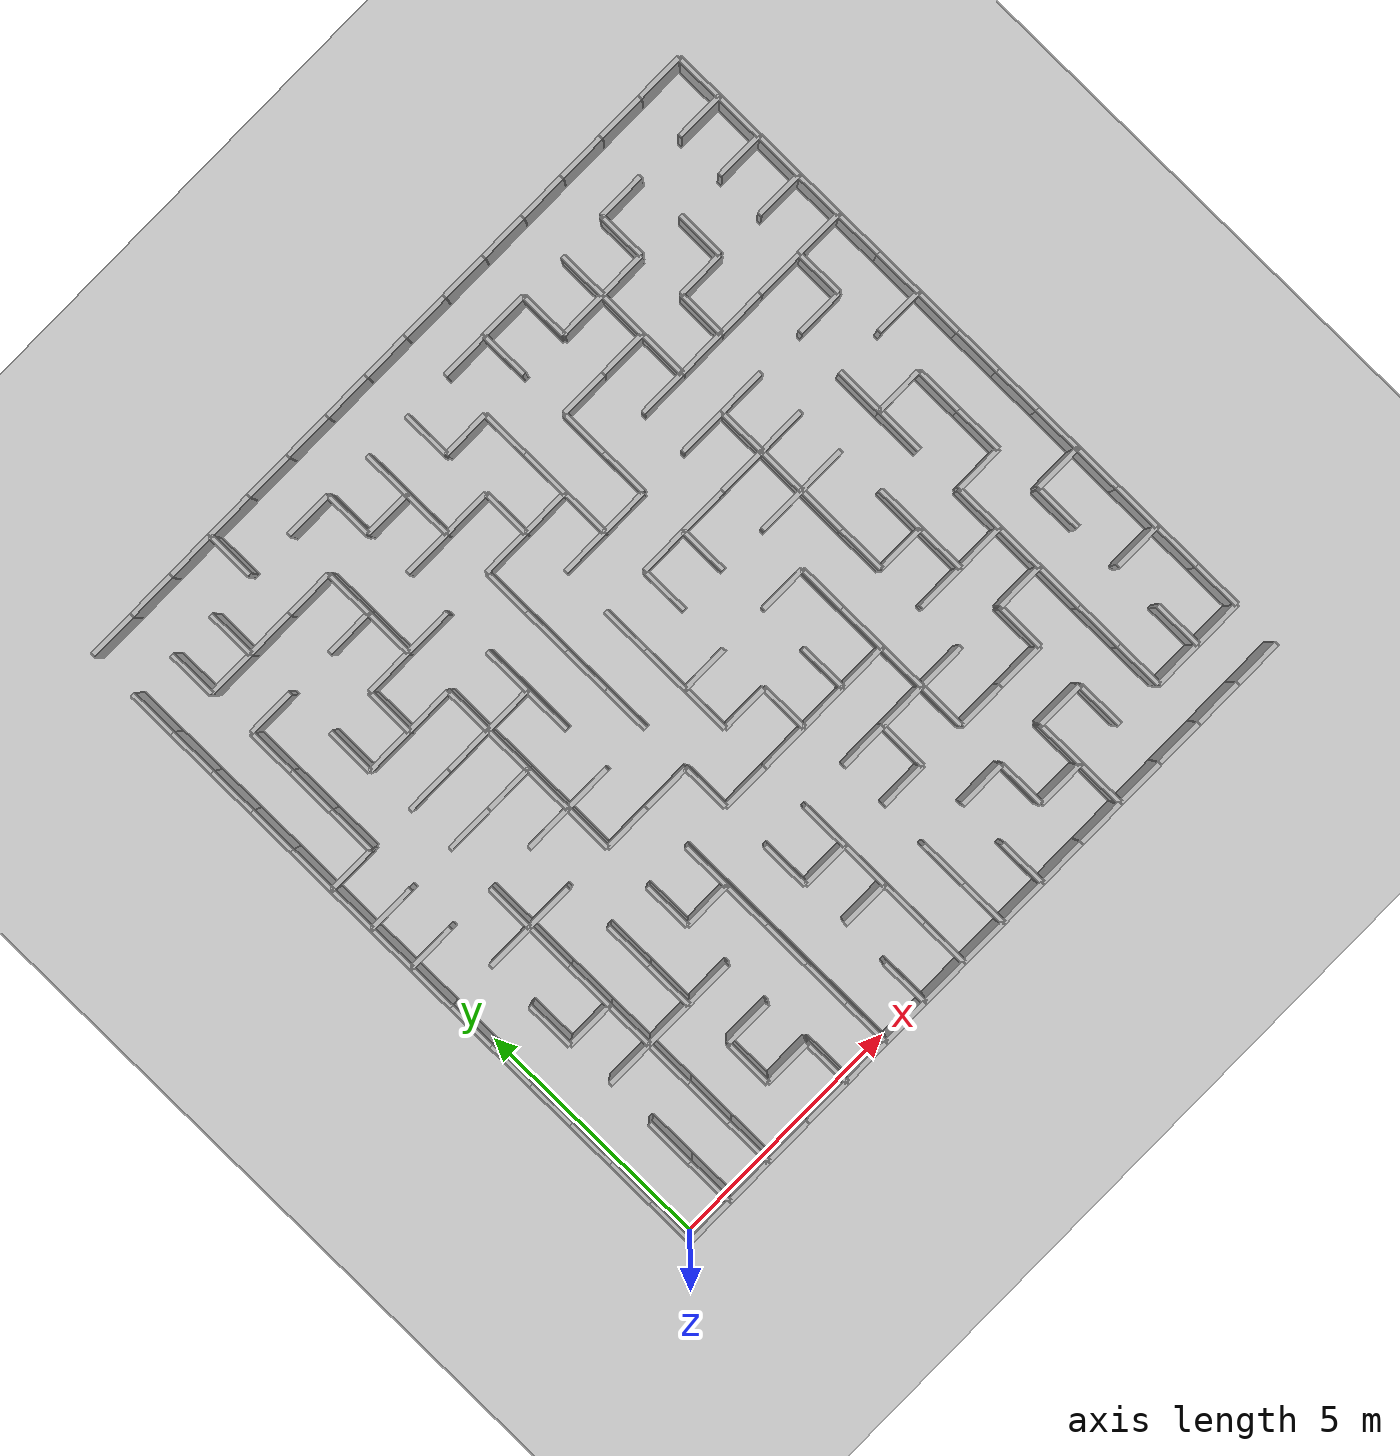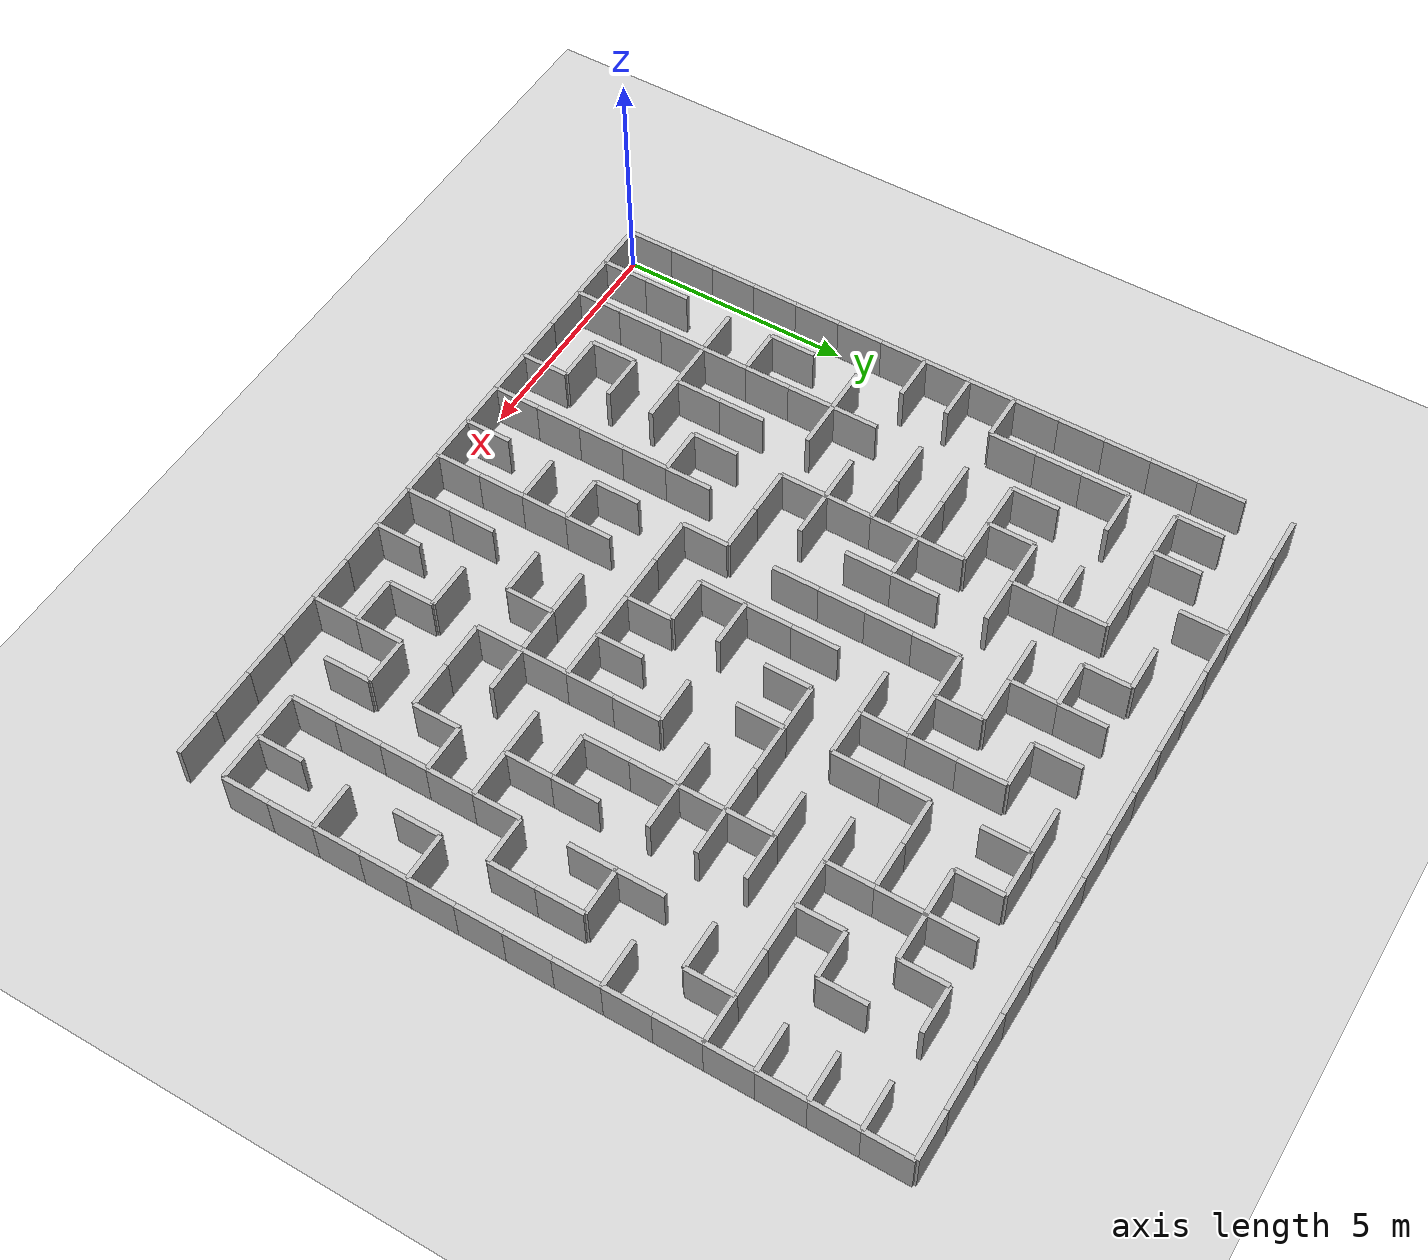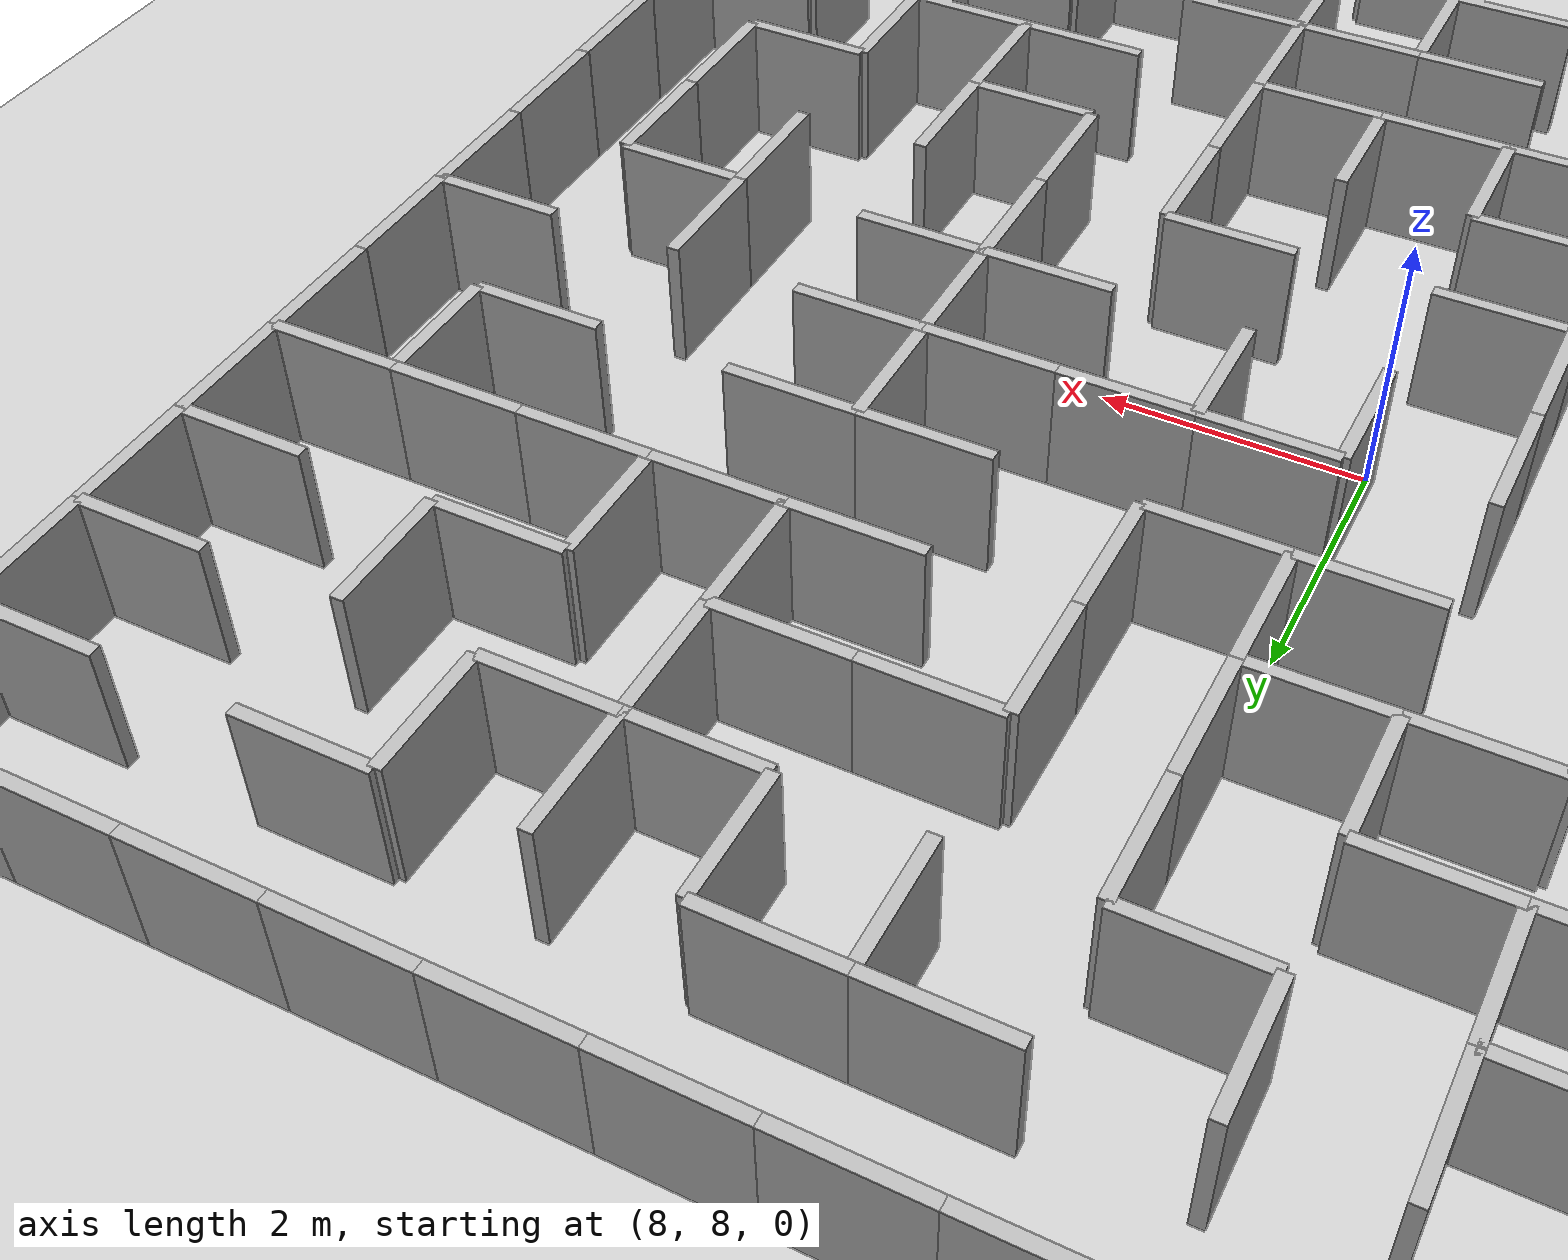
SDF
<sdf version="1.6"><world name="maze"><include><uri>model://ground_plane</uri></include><model name="wall_r0_c0_N_b"><static>true</static><pose>0.5 15.0 0.5 0 0 0</pose><link name="link"><collision name="collision"><geometry><box><size>1.0 0.1 1.0</size></box></geometry></collision><visual name="visual"><geometry><box><size>1.0 0.1 1.0</size></box></geometry></visual></link></model><model name="wall_r0_c1_N_b"><static>true</static><pose>1.5 15.0 0.5 0 0 0</pose><link name="link"><collision name="collision"><geometry><box><size>1.0 0.1 1.0</size></box></geometry></collision><visual name="visual"><geometry><box><size>1.0 0.1 1.0</size></box></geometry></visual></link></model><model name="wall_r0_c2_N_b"><static>true</static><pose>2.5 15.0 0.5 0 0 0</pose><link name="link"><collision name="collision"><geometry><box><size>1.0 0.1 1.0</size></box></geometry></collision><visual name="visual"><geometry><box><size>1.0 0.1 1.0</size></box></geometry></visual></link></model><model name="wall_r0_c3_N_b"><static>true</static><pose>3.5 15.0 0.5 0 0 0</pose><link name="link"><collision name="collision"><geometry><box><size>1.0 0.1 1.0</size></box></geometry></collision><visual name="visual"><geometry><box><size>1.0 0.1 1.0</size></box></geometry></visual></link></model><model name="wall_r0_c3_W"><static>true</static><pose>3.0 14.5 0.5 0 0 0</pose><link name="link"><collision name="collision"><geometry><box><size>0.1 1.0 1.0</size></box></geometry></collision><visual name="visual"><geometry><box><size>0.1 1.0 1.0</size></box></geometry></visual></link></model><model name="wall_r0_c4_N_b"><static>true</static><pose>4.5 15.0 0.5 0 0 0</pose><link name="link"><collision name="collision"><geometry><box><size>1.0 0.1 1.0</size></box></geometry></collision><visual name="visual"><geometry><box><size>1.0 0.1 1.0</size></box></geometry></visual></link></model><model name="wall_r0_c5_N_b"><static>true</static><pose>5.5 15.0 0.5 0 0 0</pose><link name="link"><collision name="collision"><geometry><box><size>1.0 0.1 1.0</size></box></geometry></collision><visual name="visual"><geometry><box><size>1.0 0.1 1.0</size></box></geometry></visual></link></model><model name="wall_r0_c6_N_b"><static>true</static><pose>6.5 15.0 0.5 0 0 0</pose><link name="link"><collision name="collision"><geometry><box><size>1.0 0.1 1.0</size></box></geometry></collision><visual name="visual"><geometry><box><size>1.0 0.1 1.0</size></box></geometry></visual></link></model><model name="wall_r0_c7_N_b"><static>true</static><pose>7.5 15.0 0.5 0 0 0</pose><link name="link"><collision name="collision"><geometry><box><size>1.0 0.1 1.0</size></box></geometry></collision><visual name="visual"><geometry><box><size>1.0 0.1 1.0</size></box></geometry></visual></link></model><model name="wall_r0_c8_N_b"><static>true</static><pose>8.5 15.0 0.5 0 0 0</pose><link name="link"><collision name="collision"><geometry><box><size>1.0 0.1 1.0</size></box></geometry></collision><visual name="visual"><geometry><box><size>1.0 0.1 1.0</size></box></geometry></visual></link></model><model name="wall_r0_c9_N_b"><static>true</static><pose>9.5 15.0 0.5 0 0 0</pose><link name="link"><collision name="collision"><geometry><box><size>1.0 0.1 1.0</size></box></geometry></collision><visual name="visual"><geometry><box><size>1.0 0.1 1.0</size></box></geometry></visual></link></model><model name="wall_r0_c10_N_b"><static>true</static><pose>10.5 15.0 0.5 0 0 0</pose><link name="link"><collision name="collision"><geometry><box><size>1.0 0.1 1.0</size></box></geometry></collision><visual name="visual"><geometry><box><size>1.0 0.1 1.0</size></box></geometry></visual></link></model><model name="wall_r0_c11_N_b"><static>true</static><pose>11.5 15.0 0.5 0 0 0</pose><link name="link"><collision name="collision"><geometry><box><size>1.0 0.1 1.0</size></box></geometry></collision><visual name="visual"><geometry><box><size>1.0 0.1 1.0</size></box></geometry></visual></link></model><model name="wall_r0_c12_N_b"><static>true</static><pose>12.5 15.0 0.5 0 0 0</pose><link name="link"><collision name="collision"><geometry><box><size>1.0 0.1 1.0</size></box></geometry></collision><visual name="visual"><geometry><box><size>1.0 0.1 1.0</size></box></geometry></visual></link></model><model name="wall_r0_c13_N_b"><static>true</static><pose>13.5 15.0 0.5 0 0 0</pose><link name="link"><collision name="collision"><geometry><box><size>1.0 0.1 1.0</size></box></geometry></collision><visual name="visual"><geometry><box><size>1.0 0.1 1.0</size></box></geometry></visual></link></model><model name="wall_r0_c14_N_b"><static>true</static><pose>14.5 15.0 0.5 0 0 0</pose><link name="link"><collision name="collision"><geometry><box><size>1.0 0.1 1.0</size></box></geometry></collision><visual name="visual"><geometry><box><size>1.0 0.1 1.0</size></box></geometry></visual></link></model><model name="wall_r0_c14_E_b"><static>true</static><pose>15.0 14.5 0.5 0 0 0</pose><link name="link"><collision name="collision"><geometry><box><size>0.1 1.0 1.0</size></box></geometry></collision><visual name="visual"><geometry><box><size>0.1 1.0 1.0</size></box></geometry></visual></link></model><model name="wall_r1_c0_W_b"><static>true</static><pose>0.0 13.5 0.5 0 0 0</pose><link name="link"><collision name="collision"><geometry><box><size>0.1 1.0 1.0</size></box></geometry></collision><visual name="visual"><geometry><box><size>0.1 1.0 1.0</size></box></geometry></visual></link></model><model name="wall_r1_c1_W"><static>true</static><pose>1.0 13.5 0.5 0 0 0</pose><link name="link"><collision name="collision"><geometry><box><size>0.1 1.0 1.0</size></box></geometry></collision><visual name="visual"><geometry><box><size>0.1 1.0 1.0</size></box></geometry></visual></link></model><model name="wall_r1_c2_W"><static>true</static><pose>2.0 13.5 0.5 0 0 0</pose><link name="link"><collision name="collision"><geometry><box><size>0.1 1.0 1.0</size></box></geometry></collision><visual name="visual"><geometry><box><size>0.1 1.0 1.0</size></box></geometry></visual></link></model><model name="wall_r1_c4_N"><static>true</static><pose>4.5 14.0 0.5 0 0 0</pose><link name="link"><collision name="collision"><geometry><box><size>1.0 0.1 1.0</size></box></geometry></collision><visual name="visual"><geometry><box><size>1.0 0.1 1.0</size></box></geometry></visual></link></model><model name="wall_r1_c5_W"><static>true</static><pose>5.0 13.5 0.5 0 0 0</pose><link name="link"><collision name="collision"><geometry><box><size>0.1 1.0 1.0</size></box></geometry></collision><visual name="visual"><geometry><box><size>0.1 1.0 1.0</size></box></geometry></visual></link></model><model name="wall_r1_c6_W"><static>true</static><pose>6.0 13.5 0.5 0 0 0</pose><link name="link"><collision name="collision"><geometry><box><size>0.1 1.0 1.0</size></box></geometry></collision><visual name="visual"><geometry><box><size>0.1 1.0 1.0</size></box></geometry></visual></link></model><model name="wall_r1_c7_W"><static>true</static><pose>7.0 13.5 0.5 0 0 0</pose><link name="link"><collision name="collision"><geometry><box><size>0.1 1.0 1.0</size></box></geometry></collision><visual name="visual"><geometry><box><size>0.1 1.0 1.0</size></box></geometry></visual></link></model><model name="wall_r1_c8_N"><static>true</static><pose>8.5 14.0 0.5 0 0 0</pose><link name="link"><collision name="collision"><geometry><box><size>1.0 0.1 1.0</size></box></geometry></collision><visual name="visual"><geometry><box><size>1.0 0.1 1.0</size></box></geometry></visual></link></model><model name="wall_r1_c9_N"><static>true</static><pose>9.5 14.0 0.5 0 0 0</pose><link name="link"><collision name="collision"><geometry><box><size>1.0 0.1 1.0</size></box></geometry></collision><visual name="visual"><geometry><box><size>1.0 0.1 1.0</size></box></geometry></visual></link></model><model name="wall_r1_c9_W"><static>true</static><pose>9.0 13.5 0.5 0 0 0</pose><link name="link"><collision name="collision"><geometry><box><size>0.1 1.0 1.0</size></box></geometry></collision><visual name="visual"><geometry><box><size>0.1 1.0 1.0</size></box></geometry></visual></link></model><model name="wall_r1_c10_W"><static>true</static><pose>10.0 13.5 0.5 0 0 0</pose><link name="link"><collision name="collision"><geometry><box><size>0.1 1.0 1.0</size></box></geometry></collision><visual name="visual"><geometry><box><size>0.1 1.0 1.0</size></box></geometry></visual></link></model><model name="wall_r1_c11_W"><static>true</static><pose>11.0 13.5 0.5 0 0 0</pose><link name="link"><collision name="collision"><geometry><box><size>0.1 1.0 1.0</size></box></geometry></collision><visual name="visual"><geometry><box><size>0.1 1.0 1.0</size></box></geometry></visual></link></model><model name="wall_r1_c12_N"><static>true</static><pose>12.5 14.0 0.5 0 0 0</pose><link name="link"><collision name="collision"><geometry><box><size>1.0 0.1 1.0</size></box></geometry></collision><visual name="visual"><geometry><box><size>1.0 0.1 1.0</size></box></geometry></visual></link></model><model name="wall_r1_c12_W"><static>true</static><pose>12.0 13.5 0.5 0 0 0</pose><link name="link"><collision name="collision"><geometry><box><size>0.1 1.0 1.0</size></box></geometry></collision><visual name="visual"><geometry><box><size>0.1 1.0 1.0</size></box></geometry></visual></link></model><model name="wall_r1_c14_N"><static>true</static><pose>14.5 14.0 0.5 0 0 0</pose><link name="link"><collision name="collision"><geometry><box><size>1.0 0.1 1.0</size></box></geometry></collision><visual name="visual"><geometry><box><size>1.0 0.1 1.0</size></box></geometry></visual></link></model><model name="wall_r1_c14_E_b"><static>true</static><pose>15.0 13.5 0.5 0 0 0</pose><link name="link"><collision name="collision"><geometry><box><size>0.1 1.0 1.0</size></box></geometry></collision><visual name="visual"><geometry><box><size>0.1 1.0 1.0</size></box></geometry></visual></link></model><model name="wall_r2_c0_W_b"><static>true</static><pose>0.0 12.5 0.5 0 0 0</pose><link name="link"><collision name="collision"><geometry><box><size>0.1 1.0 1.0</size></box></geometry></collision><visual name="visual"><geometry><box><size>0.1 1.0 1.0</size></box></geometry></visual></link></model><model name="wall_r2_c1_N"><static>true</static><pose>1.5 13.0 0.5 0 0 0</pose><link name="link"><collision name="collision"><geometry><box><size>1.0 0.1 1.0</size></box></geometry></collision><visual name="visual"><geometry><box><size>1.0 0.1 1.0</size></box></geometry></visual></link></model><model name="wall_r2_c2_N"><static>true</static><pose>2.5 13.0 0.5 0 0 0</pose><link name="link"><collision name="collision"><geometry><box><size>1.0 0.1 1.0</size></box></geometry></collision><visual name="visual"><geometry><box><size>1.0 0.1 1.0</size></box></geometry></visual></link></model><model name="wall_r2_c3_N"><static>true</static><pose>3.5 13.0 0.5 0 0 0</pose><link name="link"><collision name="collision"><geometry><box><size>1.0 0.1 1.0</size></box></geometry></collision><visual name="visual"><geometry><box><size>1.0 0.1 1.0</size></box></geometry></visual></link></model><model name="wall_r2_c4_W"><static>true</static><pose>4.0 12.5 0.5 0 0 0</pose><link name="link"><collision name="collision"><geometry><box><size>0.1 1.0 1.0</size></box></geometry></collision><visual name="visual"><geometry><box><size>0.1 1.0 1.0</size></box></geometry></visual></link></model><model name="wall_r2_c5_N"><static>true</static><pose>5.5 13.0 0.5 0 0 0</pose><link name="link"><collision name="collision"><geometry><box><size>1.0 0.1 1.0</size></box></geometry></collision><visual name="visual"><geometry><box><size>1.0 0.1 1.0</size></box></geometry></visual></link></model><model name="wall_r2_c6_W"><static>true</static><pose>6.0 12.5 0.5 0 0 0</pose><link name="link"><collision name="collision"><geometry><box><size>0.1 1.0 1.0</size></box></geometry></collision><visual name="visual"><geometry><box><size>0.1 1.0 1.0</size></box></geometry></visual></link></model><model name="wall_r2_c7_N"><static>true</static><pose>7.5 13.0 0.5 0 0 0</pose><link name="link"><collision name="collision"><geometry><box><size>1.0 0.1 1.0</size></box></geometry></collision><visual name="visual"><geometry><box><size>1.0 0.1 1.0</size></box></geometry></visual></link></model><model name="wall_r2_c8_W"><static>true</static><pose>8.0 12.5 0.5 0 0 0</pose><link name="link"><collision name="collision"><geometry><box><size>0.1 1.0 1.0</size></box></geometry></collision><visual name="visual"><geometry><box><size>0.1 1.0 1.0</size></box></geometry></visual></link></model><model name="wall_r2_c10_N"><static>true</static><pose>10.5 13.0 0.5 0 0 0</pose><link name="link"><collision name="collision"><geometry><box><size>1.0 0.1 1.0</size></box></geometry></collision><visual name="visual"><geometry><box><size>1.0 0.1 1.0</size></box></geometry></visual></link></model><model name="wall_r2_c11_N"><static>true</static><pose>11.5 13.0 0.5 0 0 0</pose><link name="link"><collision name="collision"><geometry><box><size>1.0 0.1 1.0</size></box></geometry></collision><visual name="visual"><geometry><box><size>1.0 0.1 1.0</size></box></geometry></visual></link></model><model name="wall_r2_c11_W"><static>true</static><pose>11.0 12.5 0.5 0 0 0</pose><link name="link"><collision name="collision"><geometry><box><size>0.1 1.0 1.0</size></box></geometry></collision><visual name="visual"><geometry><box><size>0.1 1.0 1.0</size></box></geometry></visual></link></model><model name="wall_r2_c13_W"><static>true</static><pose>13.0 12.5 0.5 0 0 0</pose><link name="link"><collision name="collision"><geometry><box><size>0.1 1.0 1.0</size></box></geometry></collision><visual name="visual"><geometry><box><size>0.1 1.0 1.0</size></box></geometry></visual></link></model><model name="wall_r2_c14_N"><static>true</static><pose>14.5 13.0 0.5 0 0 0</pose><link name="link"><collision name="collision"><geometry><box><size>1.0 0.1 1.0</size></box></geometry></collision><visual name="visual"><geometry><box><size>1.0 0.1 1.0</size></box></geometry></visual></link></model><model name="wall_r2_c14_E_b"><static>true</static><pose>15.0 12.5 0.5 0 0 0</pose><link name="link"><collision name="collision"><geometry><box><size>0.1 1.0 1.0</size></box></geometry></collision><visual name="visual"><geometry><box><size>0.1 1.0 1.0</size></box></geometry></visual></link></model><model name="wall_r3_c0_W_b"><static>true</static><pose>0.0 11.5 0.5 0 0 0</pose><link name="link"><collision name="collision"><geometry><box><size>0.1 1.0 1.0</size></box></geometry></collision><visual name="visual"><geometry><box><size>0.1 1.0 1.0</size></box></geometry></visual></link></model><model name="wall_r3_c1_N"><static>true</static><pose>1.5 12.0 0.5 0 0 0</pose><link name="link"><collision name="collision"><geometry><box><size>1.0 0.1 1.0</size></box></geometry></collision><visual name="visual"><geometry><box><size>1.0 0.1 1.0</size></box></geometry></visual></link></model><model name="wall_r3_c1_W"><static>true</static><pose>1.0 11.5 0.5 0 0 0</pose><link name="link"><collision name="collision"><geometry><box><size>0.1 1.0 1.0</size></box></geometry></collision><visual name="visual"><geometry><box><size>0.1 1.0 1.0</size></box></geometry></visual></link></model><model name="wall_r3_c3_N"><static>true</static><pose>3.5 12.0 0.5 0 0 0</pose><link name="link"><collision name="collision"><geometry><box><size>1.0 0.1 1.0</size></box></geometry></collision><visual name="visual"><geometry><box><size>1.0 0.1 1.0</size></box></geometry></visual></link></model><model name="wall_r3_c4_W"><static>true</static><pose>4.0 11.5 0.5 0 0 0</pose><link name="link"><collision name="collision"><geometry><box><size>0.1 1.0 1.0</size></box></geometry></collision><visual name="visual"><geometry><box><size>0.1 1.0 1.0</size></box></geometry></visual></link></model><model name="wall_r3_c5_N"><static>true</static><pose>5.5 12.0 0.5 0 0 0</pose><link name="link"><collision name="collision"><geometry><box><size>1.0 0.1 1.0</size></box></geometry></collision><visual name="visual"><geometry><box><size>1.0 0.1 1.0</size></box></geometry></visual></link></model><model name="wall_r3_c6_N"><static>true</static><pose>6.5 12.0 0.5 0 0 0</pose><link name="link"><collision name="collision"><geometry><box><size>1.0 0.1 1.0</size></box></geometry></collision><visual name="visual"><geometry><box><size>1.0 0.1 1.0</size></box></geometry></visual></link></model><model name="wall_r3_c7_W"><static>true</static><pose>7.0 11.5 0.5 0 0 0</pose><link name="link"><collision name="collision"><geometry><box><size>0.1 1.0 1.0</size></box></geometry></collision><visual name="visual"><geometry><box><size>0.1 1.0 1.0</size></box></geometry></visual></link></model><model name="wall_r3_c8_W"><static>true</static><pose>8.0 11.5 0.5 0 0 0</pose><link name="link"><collision name="collision"><geometry><box><size>0.1 1.0 1.0</size></box></geometry></collision><visual name="visual"><geometry><box><size>0.1 1.0 1.0</size></box></geometry></visual></link></model><model name="wall_r3_c9_N"><static>true</static><pose>9.5 12.0 0.5 0 0 0</pose><link name="link"><collision name="collision"><geometry><box><size>1.0 0.1 1.0</size></box></geometry></collision><visual name="visual"><geometry><box><size>1.0 0.1 1.0</size></box></geometry></visual></link></model><model name="wall_r3_c9_W"><static>true</static><pose>9.0 11.5 0.5 0 0 0</pose><link name="link"><collision name="collision"><geometry><box><size>0.1 1.0 1.0</size></box></geometry></collision><visual name="visual"><geometry><box><size>0.1 1.0 1.0</size></box></geometry></visual></link></model><model name="wall_r3_c10_N"><static>true</static><pose>10.5 12.0 0.5 0 0 0</pose><link name="link"><collision name="collision"><geometry><box><size>1.0 0.1 1.0</size></box></geometry></collision><visual name="visual"><geometry><box><size>1.0 0.1 1.0</size></box></geometry></visual></link></model><model name="wall_r3_c11_W"><static>true</static><pose>11.0 11.5 0.5 0 0 0</pose><link name="link"><collision name="collision"><geometry><box><size>0.1 1.0 1.0</size></box></geometry></collision><visual name="visual"><geometry><box><size>0.1 1.0 1.0</size></box></geometry></visual></link></model><model name="wall_r3_c12_N"><static>true</static><pose>12.5 12.0 0.5 0 0 0</pose><link name="link"><collision name="collision"><geometry><box><size>1.0 0.1 1.0</size></box></geometry></collision><visual name="visual"><geometry><box><size>1.0 0.1 1.0</size></box></geometry></visual></link></model><model name="wall_r3_c12_W"><static>true</static><pose>12.0 11.5 0.5 0 0 0</pose><link name="link"><collision name="collision"><geometry><box><size>0.1 1.0 1.0</size></box></geometry></collision><visual name="visual"><geometry><box><size>0.1 1.0 1.0</size></box></geometry></visual></link></model><model name="wall_r3_c14_N"><static>true</static><pose>14.5 12.0 0.5 0 0 0</pose><link name="link"><collision name="collision"><geometry><box><size>1.0 0.1 1.0</size></box></geometry></collision><visual name="visual"><geometry><box><size>1.0 0.1 1.0</size></box></geometry></visual></link></model><model name="wall_r3_c14_E_b"><static>true</static><pose>15.0 11.5 0.5 0 0 0</pose><link name="link"><collision name="collision"><geometry><box><size>0.1 1.0 1.0</size></box></geometry></collision><visual name="visual"><geometry><box><size>0.1 1.0 1.0</size></box></geometry></visual></link></model><model name="wall_r4_c0_W_b"><static>true</static><pose>0.0 10.5 0.5 0 0 0</pose><link name="link"><collision name="collision"><geometry><box><size>0.1 1.0 1.0</size></box></geometry></collision><visual name="visual"><geometry><box><size>0.1 1.0 1.0</size></box></geometry></visual></link></model><model name="wall_r4_c1_W"><static>true</static><pose>1.0 10.5 0.5 0 0 0</pose><link name="link"><collision name="collision"><geometry><box><size>0.1 1.0 1.0</size></box></geometry></collision><visual name="visual"><geometry><box><size>0.1 1.0 1.0</size></box></geometry></visual></link></model><model name="wall_r4_c2_W"><static>true</static><pose>2.0 10.5 0.5 0 0 0</pose><link name="link"><collision name="collision"><geometry><box><size>0.1 1.0 1.0</size></box></geometry></collision><visual name="visual"><geometry><box><size>0.1 1.0 1.0</size></box></geometry></visual></link></model><model name="wall_r4_c3_N"><static>true</static><pose>3.5 11.0 0.5 0 0 0</pose><link name="link"><collision name="collision"><geometry><box><size>1.0 0.1 1.0</size></box></geometry></collision><visual name="visual"><geometry><box><size>1.0 0.1 1.0</size></box></geometry></visual></link></model><model name="wall_r4_c3_W"><static>true</static><pose>3.0 10.5 0.5 0 0 0</pose><link name="link"><collision name="collision"><geometry><box><size>0.1 1.0 1.0</size></box></geometry></collision><visual name="visual"><geometry><box><size>0.1 1.0 1.0</size></box></geometry></visual></link></model><model name="wall_r4_c4_N"><static>true</static><pose>4.5 11.0 0.5 0 0 0</pose><link name="link"><collision name="collision"><geometry><box><size>1.0 0.1 1.0</size></box></geometry></collision><visual name="visual"><geometry><box><size>1.0 0.1 1.0</size></box></geometry></visual></link></model><model name="wall_r4_c6_N"><static>true</static><pose>6.5 11.0 0.5 0 0 0</pose><link name="link"><collision name="collision"><geometry><box><size>1.0 0.1 1.0</size></box></geometry></collision><visual name="visual"><geometry><box><size>1.0 0.1 1.0</size></box></geometry></visual></link></model><model name="wall_r4_c6_W"><static>true</static><pose>6.0 10.5 0.5 0 0 0</pose><link name="link"><collision name="collision"><geometry><box><size>0.1 1.0 1.0</size></box></geometry></collision><visual name="visual"><geometry><box><size>0.1 1.0 1.0</size></box></geometry></visual></link></model><model name="wall_r4_c7_N"><static>true</static><pose>7.5 11.0 0.5 0 0 0</pose><link name="link"><collision name="collision"><geometry><box><size>1.0 0.1 1.0</size></box></geometry></collision><visual name="visual"><geometry><box><size>1.0 0.1 1.0</size></box></geometry></visual></link></model><model name="wall_r4_c8_W"><static>true</static><pose>8.0 10.5 0.5 0 0 0</pose><link name="link"><collision name="collision"><geometry><box><size>0.1 1.0 1.0</size></box></geometry></collision><visual name="visual"><geometry><box><size>0.1 1.0 1.0</size></box></geometry></visual></link></model><model name="wall_r4_c9_W"><static>true</static><pose>9.0 10.5 0.5 0 0 0</pose><link name="link"><collision name="collision"><geometry><box><size>0.1 1.0 1.0</size></box></geometry></collision><visual name="visual"><geometry><box><size>0.1 1.0 1.0</size></box></geometry></visual></link></model><model name="wall_r4_c10_N"><static>true</static><pose>10.5 11.0 0.5 0 0 0</pose><link name="link"><collision name="collision"><geometry><box><size>1.0 0.1 1.0</size></box></geometry></collision><visual name="visual"><geometry><box><size>1.0 0.1 1.0</size></box></geometry></visual></link></model><model name="wall_r4_c11_N"><static>true</static><pose>11.5 11.0 0.5 0 0 0</pose><link name="link"><collision name="collision"><geometry><box><size>1.0 0.1 1.0</size></box></geometry></collision><visual name="visual"><geometry><box><size>1.0 0.1 1.0</size></box></geometry></visual></link></model><model name="wall_r4_c12_N"><static>true</static><pose>12.5 11.0 0.5 0 0 0</pose><link name="link"><collision name="collision"><geometry><box><size>1.0 0.1 1.0</size></box></geometry></collision><visual name="visual"><geometry><box><size>1.0 0.1 1.0</size></box></geometry></visual></link></model><model name="wall_r4_c13_N"><static>true</static><pose>13.5 11.0 0.5 0 0 0</pose><link name="link"><collision name="collision"><geometry><box><size>1.0 0.1 1.0</size></box></geometry></collision><visual name="visual"><geometry><box><size>1.0 0.1 1.0</size></box></geometry></visual></link></model><model name="wall_r4_c14_N"><static>true</static><pose>14.5 11.0 0.5 0 0 0</pose><link name="link"><collision name="collision"><geometry><box><size>1.0 0.1 1.0</size></box></geometry></collision><visual name="visual"><geometry><box><size>1.0 0.1 1.0</size></box></geometry></visual></link></model><model name="wall_r4_c14_W"><static>true</static><pose>14.0 10.5 0.5 0 0 0</pose><link name="link"><collision name="collision"><geometry><box><size>0.1 1.0 1.0</size></box></geometry></collision><visual name="visual"><geometry><box><size>0.1 1.0 1.0</size></box></geometry></visual></link></model><model name="wall_r4_c14_E_b"><static>true</static><pose>15.0 10.5 0.5 0 0 0</pose><link name="link"><collision name="collision"><geometry><box><size>0.1 1.0 1.0</size></box></geometry></collision><visual name="visual"><geometry><box><size>0.1 1.0 1.0</size></box></geometry></visual></link></model><model name="wall_r5_c0_W_b"><static>true</static><pose>0.0 9.5 0.5 0 0 0</pose><link name="link"><collision name="collision"><geometry><box><size>0.1 1.0 1.0</size></box></geometry></collision><visual name="visual"><geometry><box><size>0.1 1.0 1.0</size></box></geometry></visual></link></model><model name="wall_r5_c1_W"><static>true</static><pose>1.0 9.5 0.5 0 0 0</pose><link name="link"><collision name="collision"><geometry><box><size>0.1 1.0 1.0</size></box></geometry></collision><visual name="visual"><geometry><box><size>0.1 1.0 1.0</size></box></geometry></visual></link></model><model name="wall_r5_c2_N"><static>true</static><pose>2.5 10.0 0.5 0 0 0</pose><link name="link"><collision name="collision"><geometry><box><size>1.0 0.1 1.0</size></box></geometry></collision><visual name="visual"><geometry><box><size>1.0 0.1 1.0</size></box></geometry></visual></link></model><model name="wall_r5_c3_N"><static>true</static><pose>3.5 10.0 0.5 0 0 0</pose><link name="link"><collision name="collision"><geometry><box><size>1.0 0.1 1.0</size></box></geometry></collision><visual name="visual"><geometry><box><size>1.0 0.1 1.0</size></box></geometry></visual></link></model><model name="wall_r5_c4_W"><static>true</static><pose>4.0 9.5 0.5 0 0 0</pose><link name="link"><collision name="collision"><geometry><box><size>0.1 1.0 1.0</size></box></geometry></collision><visual name="visual"><geometry><box><size>0.1 1.0 1.0</size></box></geometry></visual></link></model><model name="wall_r5_c5_W"><static>true</static><pose>5.0 9.5 0.5 0 0 0</pose><link name="link"><collision name="collision"><geometry><box><size>0.1 1.0 1.0</size></box></geometry></collision><visual name="visual"><geometry><box><size>0.1 1.0 1.0</size></box></geometry></visual></link></model><model name="wall_r5_c6_W"><static>true</static><pose>6.0 9.5 0.5 0 0 0</pose><link name="link"><collision name="collision"><geometry><box><size>0.1 1.0 1.0</size></box></geometry></collision><visual name="visual"><geometry><box><size>0.1 1.0 1.0</size></box></geometry></visual></link></model><model name="wall_r5_c7_N"><static>true</static><pose>7.5 10.0 0.5 0 0 0</pose><link name="link"><collision name="collision"><geometry><box><size>1.0 0.1 1.0</size></box></geometry></collision><visual name="visual"><geometry><box><size>1.0 0.1 1.0</size></box></geometry></visual></link></model><model name="wall_r5_c8_N"><static>true</static><pose>8.5 10.0 0.5 0 0 0</pose><link name="link"><collision name="collision"><geometry><box><size>1.0 0.1 1.0</size></box></geometry></collision><visual name="visual"><geometry><box><size>1.0 0.1 1.0</size></box></geometry></visual></link></model><model name="wall_r5_c10_N"><static>true</static><pose>10.5 10.0 0.5 0 0 0</pose><link name="link"><collision name="collision"><geometry><box><size>1.0 0.1 1.0</size></box></geometry></collision><visual name="visual"><geometry><box><size>1.0 0.1 1.0</size></box></geometry></visual></link></model><model name="wall_r5_c11_N"><static>true</static><pose>11.5 10.0 0.5 0 0 0</pose><link name="link"><collision name="collision"><geometry><box><size>1.0 0.1 1.0</size></box></geometry></collision><visual name="visual"><geometry><box><size>1.0 0.1 1.0</size></box></geometry></visual></link></model><model name="wall_r5_c11_W"><static>true</static><pose>11.0 9.5 0.5 0 0 0</pose><link name="link"><collision name="collision"><geometry><box><size>0.1 1.0 1.0</size></box></geometry></collision><visual name="visual"><geometry><box><size>0.1 1.0 1.0</size></box></geometry></visual></link></model><model name="wall_r5_c13_N"><static>true</static><pose>13.5 10.0 0.5 0 0 0</pose><link name="link"><collision name="collision"><geometry><box><size>1.0 0.1 1.0</size></box></geometry></collision><visual name="visual"><geometry><box><size>1.0 0.1 1.0</size></box></geometry></visual></link></model><model name="wall_r5_c14_E_b"><static>true</static><pose>15.0 9.5 0.5 0 0 0</pose><link name="link"><collision name="collision"><geometry><box><size>0.1 1.0 1.0</size></box></geometry></collision><visual name="visual"><geometry><box><size>0.1 1.0 1.0</size></box></geometry></visual></link></model><model name="wall_r6_c0_N"><static>true</static><pose>0.5 9.0 0.5 0 0 0</pose><link name="link"><collision name="collision"><geometry><box><size>1.0 0.1 1.0</size></box></geometry></collision><visual name="visual"><geometry><box><size>1.0 0.1 1.0</size></box></geometry></visual></link></model><model name="wall_r6_c0_W_b"><static>true</static><pose>0.0 8.5 0.5 0 0 0</pose><link name="link"><collision name="collision"><geometry><box><size>0.1 1.0 1.0</size></box></geometry></collision><visual name="visual"><geometry><box><size>0.1 1.0 1.0</size></box></geometry></visual></link></model><model name="wall_r6_c2_N"><static>true</static><pose>2.5 9.0 0.5 0 0 0</pose><link name="link"><collision name="collision"><geometry><box><size>1.0 0.1 1.0</size></box></geometry></collision><visual name="visual"><geometry><box><size>1.0 0.1 1.0</size></box></geometry></visual></link></model><model name="wall_r6_c3_N"><static>true</static><pose>3.5 9.0 0.5 0 0 0</pose><link name="link"><collision name="collision"><geometry><box><size>1.0 0.1 1.0</size></box></geometry></collision><visual name="visual"><geometry><box><size>1.0 0.1 1.0</size></box></geometry></visual></link></model><model name="wall_r6_c4_N"><static>true</static><pose>4.5 9.0 0.5 0 0 0</pose><link name="link"><collision name="collision"><geometry><box><size>1.0 0.1 1.0</size></box></geometry></collision><visual name="visual"><geometry><box><size>1.0 0.1 1.0</size></box></geometry></visual></link></model><model name="wall_r6_c4_W"><static>true</static><pose>4.0 8.5 0.5 0 0 0</pose><link name="link"><collision name="collision"><geometry><box><size>0.1 1.0 1.0</size></box></geometry></collision><visual name="visual"><geometry><box><size>0.1 1.0 1.0</size></box></geometry></visual></link></model><model name="wall_r6_c5_W"><static>true</static><pose>5.0 8.5 0.5 0 0 0</pose><link name="link"><collision name="collision"><geometry><box><size>0.1 1.0 1.0</size></box></geometry></collision><visual name="visual"><geometry><box><size>0.1 1.0 1.0</size></box></geometry></visual></link></model><model name="wall_r6_c6_W"><static>true</static><pose>6.0 8.5 0.5 0 0 0</pose><link name="link"><collision name="collision"><geometry><box><size>0.1 1.0 1.0</size></box></geometry></collision><visual name="visual"><geometry><box><size>0.1 1.0 1.0</size></box></geometry></visual></link></model><model name="wall_r6_c7_W"><static>true</static><pose>7.0 8.5 0.5 0 0 0</pose><link name="link"><collision name="collision"><geometry><box><size>0.1 1.0 1.0</size></box></geometry></collision><visual name="visual"><geometry><box><size>0.1 1.0 1.0</size></box></geometry></visual></link></model><model name="wall_r6_c8_N"><static>true</static><pose>8.5 9.0 0.5 0 0 0</pose><link name="link"><collision name="collision"><geometry><box><size>1.0 0.1 1.0</size></box></geometry></collision><visual name="visual"><geometry><box><size>1.0 0.1 1.0</size></box></geometry></visual></link></model><model name="wall_r6_c8_W"><static>true</static><pose>8.0 8.5 0.5 0 0 0</pose><link name="link"><collision name="collision"><geometry><box><size>0.1 1.0 1.0</size></box></geometry></collision><visual name="visual"><geometry><box><size>0.1 1.0 1.0</size></box></geometry></visual></link></model><model name="wall_r6_c9_N"><static>true</static><pose>9.5 9.0 0.5 0 0 0</pose><link name="link"><collision name="collision"><geometry><box><size>1.0 0.1 1.0</size></box></geometry></collision><visual name="visual"><geometry><box><size>1.0 0.1 1.0</size></box></geometry></visual></link></model><model name="wall_r6_c9_W"><static>true</static><pose>9.0 8.5 0.5 0 0 0</pose><link name="link"><collision name="collision"><geometry><box><size>0.1 1.0 1.0</size></box></geometry></collision><visual name="visual"><geometry><box><size>0.1 1.0 1.0</size></box></geometry></visual></link></model><model name="wall_r6_c10_N"><static>true</static><pose>10.5 9.0 0.5 0 0 0</pose><link name="link"><collision name="collision"><geometry><box><size>1.0 0.1 1.0</size></box></geometry></collision><visual name="visual"><geometry><box><size>1.0 0.1 1.0</size></box></geometry></visual></link></model><model name="wall_r6_c11_N"><static>true</static><pose>11.5 9.0 0.5 0 0 0</pose><link name="link"><collision name="collision"><geometry><box><size>1.0 0.1 1.0</size></box></geometry></collision><visual name="visual"><geometry><box><size>1.0 0.1 1.0</size></box></geometry></visual></link></model><model name="wall_r6_c11_W"><static>true</static><pose>11.0 8.5 0.5 0 0 0</pose><link name="link"><collision name="collision"><geometry><box><size>0.1 1.0 1.0</size></box></geometry></collision><visual name="visual"><geometry><box><size>0.1 1.0 1.0</size></box></geometry></visual></link></model><model name="wall_r6_c13_W"><static>true</static><pose>13.0 8.5 0.5 0 0 0</pose><link name="link"><collision name="collision"><geometry><box><size>0.1 1.0 1.0</size></box></geometry></collision><visual name="visual"><geometry><box><size>0.1 1.0 1.0</size></box></geometry></visual></link></model><model name="wall_r6_c14_N"><static>true</static><pose>14.5 9.0 0.5 0 0 0</pose><link name="link"><collision name="collision"><geometry><box><size>1.0 0.1 1.0</size></box></geometry></collision><visual name="visual"><geometry><box><size>1.0 0.1 1.0</size></box></geometry></visual></link></model><model name="wall_r6_c14_E_b"><static>true</static><pose>15.0 8.5 0.5 0 0 0</pose><link name="link"><collision name="collision"><geometry><box><size>0.1 1.0 1.0</size></box></geometry></collision><visual name="visual"><geometry><box><size>0.1 1.0 1.0</size></box></geometry></visual></link></model><model name="wall_r7_c0_N"><static>true</static><pose>0.5 8.0 0.5 0 0 0</pose><link name="link"><collision name="collision"><geometry><box><size>1.0 0.1 1.0</size></box></geometry></collision><visual name="visual"><geometry><box><size>1.0 0.1 1.0</size></box></geometry></visual></link></model><model name="wall_r7_c0_W_b"><static>true</static><pose>0.0 7.5 0.5 0 0 0</pose><link name="link"><collision name="collision"><geometry><box><size>0.1 1.0 1.0</size></box></geometry></collision><visual name="visual"><geometry><box><size>0.1 1.0 1.0</size></box></geometry></visual></link></model><model name="wall_r7_c2_N"><static>true</static><pose>2.5 8.0 0.5 0 0 0</pose><link name="link"><collision name="collision"><geometry><box><size>1.0 0.1 1.0</size></box></geometry></collision><visual name="visual"><geometry><box><size>1.0 0.1 1.0</size></box></geometry></visual></link></model><model name="wall_r7_c3_N"><static>true</static><pose>3.5 8.0 0.5 0 0 0</pose><link name="link"><collision name="collision"><geometry><box><size>1.0 0.1 1.0</size></box></geometry></collision><visual name="visual"><geometry><box><size>1.0 0.1 1.0</size></box></geometry></visual></link></model><model name="wall_r7_c4_W"><static>true</static><pose>4.0 7.5 0.5 0 0 0</pose><link name="link"><collision name="collision"><geometry><box><size>0.1 1.0 1.0</size></box></geometry></collision><visual name="visual"><geometry><box><size>0.1 1.0 1.0</size></box></geometry></visual></link></model><model name="wall_r7_c6_W"><static>true</static><pose>6.0 7.5 0.5 0 0 0</pose><link name="link"><collision name="collision"><geometry><box><size>0.1 1.0 1.0</size></box></geometry></collision><visual name="visual"><geometry><box><size>0.1 1.0 1.0</size></box></geometry></visual></link></model><model name="wall_r7_c7_W"><static>true</static><pose>7.0 7.5 0.5 0 0 0</pose><link name="link"><collision name="collision"><geometry><box><size>0.1 1.0 1.0</size></box></geometry></collision><visual name="visual"><geometry><box><size>0.1 1.0 1.0</size></box></geometry></visual></link></model><model name="wall_r7_c10_N"><static>true</static><pose>10.5 8.0 0.5 0 0 0</pose><link name="link"><collision name="collision"><geometry><box><size>1.0 0.1 1.0</size></box></geometry></collision><visual name="visual"><geometry><box><size>1.0 0.1 1.0</size></box></geometry></visual></link></model><model name="wall_r7_c11_N"><static>true</static><pose>11.5 8.0 0.5 0 0 0</pose><link name="link"><collision name="collision"><geometry><box><size>1.0 0.1 1.0</size></box></geometry></collision><visual name="visual"><geometry><box><size>1.0 0.1 1.0</size></box></geometry></visual></link></model><model name="wall_r7_c11_W"><static>true</static><pose>11.0 7.5 0.5 0 0 0</pose><link name="link"><collision name="collision"><geometry><box><size>0.1 1.0 1.0</size></box></geometry></collision><visual name="visual"><geometry><box><size>0.1 1.0 1.0</size></box></geometry></visual></link></model><model name="wall_r7_c13_N"><static>true</static><pose>13.5 8.0 0.5 0 0 0</pose><link name="link"><collision name="collision"><geometry><box><size>1.0 0.1 1.0</size></box></geometry></collision><visual name="visual"><geometry><box><size>1.0 0.1 1.0</size></box></geometry></visual></link></model><model name="wall_r7_c13_W"><static>true</static><pose>13.0 7.5 0.5 0 0 0</pose><link name="link"><collision name="collision"><geometry><box><size>0.1 1.0 1.0</size></box></geometry></collision><visual name="visual"><geometry><box><size>0.1 1.0 1.0</size></box></geometry></visual></link></model><model name="wall_r7_c14_W"><static>true</static><pose>14.0 7.5 0.5 0 0 0</pose><link name="link"><collision name="collision"><geometry><box><size>0.1 1.0 1.0</size></box></geometry></collision><visual name="visual"><geometry><box><size>0.1 1.0 1.0</size></box></geometry></visual></link></model><model name="wall_r7_c14_E_b"><static>true</static><pose>15.0 7.5 0.5 0 0 0</pose><link name="link"><collision name="collision"><geometry><box><size>0.1 1.0 1.0</size></box></geometry></collision><visual name="visual"><geometry><box><size>0.1 1.0 1.0</size></box></geometry></visual></link></model><model name="wall_r8_c0_N"><static>true</static><pose>0.5 7.0 0.5 0 0 0</pose><link name="link"><collision name="collision"><geometry><box><size>1.0 0.1 1.0</size></box></geometry></collision><visual name="visual"><geometry><box><size>1.0 0.1 1.0</size></box></geometry></visual></link></model><model name="wall_r8_c0_W_b"><static>true</static><pose>0.0 6.5 0.5 0 0 0</pose><link name="link"><collision name="collision"><geometry><box><size>0.1 1.0 1.0</size></box></geometry></collision><visual name="visual"><geometry><box><size>0.1 1.0 1.0</size></box></geometry></visual></link></model><model name="wall_r8_c2_W"><static>true</static><pose>2.0 6.5 0.5 0 0 0</pose><link name="link"><collision name="collision"><geometry><box><size>0.1 1.0 1.0</size></box></geometry></collision><visual name="visual"><geometry><box><size>0.1 1.0 1.0</size></box></geometry></visual></link></model><model name="wall_r8_c3_N"><static>true</static><pose>3.5 7.0 0.5 0 0 0</pose><link name="link"><collision name="collision"><geometry><box><size>1.0 0.1 1.0</size></box></geometry></collision><visual name="visual"><geometry><box><size>1.0 0.1 1.0</size></box></geometry></visual></link></model><model name="wall_r8_c4_N"><static>true</static><pose>4.5 7.0 0.5 0 0 0</pose><link name="link"><collision name="collision"><geometry><box><size>1.0 0.1 1.0</size></box></geometry></collision><visual name="visual"><geometry><box><size>1.0 0.1 1.0</size></box></geometry></visual></link></model><model name="wall_r8_c4_W"><static>true</static><pose>4.0 6.5 0.5 0 0 0</pose><link name="link"><collision name="collision"><geometry><box><size>0.1 1.0 1.0</size></box></geometry></collision><visual name="visual"><geometry><box><size>0.1 1.0 1.0</size></box></geometry></visual></link></model><model name="wall_r8_c7_N"><static>true</static><pose>7.5 7.0 0.5 0 0 0</pose><link name="link"><collision name="collision"><geometry><box><size>1.0 0.1 1.0</size></box></geometry></collision><visual name="visual"><geometry><box><size>1.0 0.1 1.0</size></box></geometry></visual></link></model><model name="wall_r8_c7_W"><static>true</static><pose>7.0 6.5 0.5 0 0 0</pose><link name="link"><collision name="collision"><geometry><box><size>0.1 1.0 1.0</size></box></geometry></collision><visual name="visual"><geometry><box><size>0.1 1.0 1.0</size></box></geometry></visual></link></model><model name="wall_r8_c9_N"><static>true</static><pose>9.5 7.0 0.5 0 0 0</pose><link name="link"><collision name="collision"><geometry><box><size>1.0 0.1 1.0</size></box></geometry></collision><visual name="visual"><geometry><box><size>1.0 0.1 1.0</size></box></geometry></visual></link></model><model name="wall_r8_c10_W"><static>true</static><pose>10.0 6.5 0.5 0 0 0</pose><link name="link"><collision name="collision"><geometry><box><size>0.1 1.0 1.0</size></box></geometry></collision><visual name="visual"><geometry><box><size>0.1 1.0 1.0</size></box></geometry></visual></link></model><model name="wall_r8_c11_W"><static>true</static><pose>11.0 6.5 0.5 0 0 0</pose><link name="link"><collision name="collision"><geometry><box><size>0.1 1.0 1.0</size></box></geometry></collision><visual name="visual"><geometry><box><size>0.1 1.0 1.0</size></box></geometry></visual></link></model><model name="wall_r8_c12_W"><static>true</static><pose>12.0 6.5 0.5 0 0 0</pose><link name="link"><collision name="collision"><geometry><box><size>0.1 1.0 1.0</size></box></geometry></collision><visual name="visual"><geometry><box><size>0.1 1.0 1.0</size></box></geometry></visual></link></model><model name="wall_r8_c14_W"><static>true</static><pose>14.0 6.5 0.5 0 0 0</pose><link name="link"><collision name="collision"><geometry><box><size>0.1 1.0 1.0</size></box></geometry></collision><visual name="visual"><geometry><box><size>0.1 1.0 1.0</size></box></geometry></visual></link></model><model name="wall_r8_c14_E_b"><static>true</static><pose>15.0 6.5 0.5 0 0 0</pose><link name="link"><collision name="collision"><geometry><box><size>0.1 1.0 1.0</size></box></geometry></collision><visual name="visual"><geometry><box><size>0.1 1.0 1.0</size></box></geometry></visual></link></model><model name="wall_r9_c0_W_b"><static>true</static><pose>0.0 5.5 0.5 0 0 0</pose><link name="link"><collision name="collision"><geometry><box><size>0.1 1.0 1.0</size></box></geometry></collision><visual name="visual"><geometry><box><size>0.1 1.0 1.0</size></box></geometry></visual></link></model><model name="wall_r9_c1_N"><static>true</static><pose>1.5 6.0 0.5 0 0 0</pose><link name="link"><collision name="collision"><geometry><box><size>1.0 0.1 1.0</size></box></geometry></collision><visual name="visual"><geometry><box><size>1.0 0.1 1.0</size></box></geometry></visual></link></model><model name="wall_r9_c2_N"><static>true</static><pose>2.5 6.0 0.5 0 0 0</pose><link name="link"><collision name="collision"><geometry><box><size>1.0 0.1 1.0</size></box></geometry></collision><visual name="visual"><geometry><box><size>1.0 0.1 1.0</size></box></geometry></visual></link></model><model name="wall_r9_c2_W"><static>true</static><pose>2.0 5.5 0.5 0 0 0</pose><link name="link"><collision name="collision"><geometry><box><size>0.1 1.0 1.0</size></box></geometry></collision><visual name="visual"><geometry><box><size>0.1 1.0 1.0</size></box></geometry></visual></link></model><model name="wall_r9_c4_N"><static>true</static><pose>4.5 6.0 0.5 0 0 0</pose><link name="link"><collision name="collision"><geometry><box><size>1.0 0.1 1.0</size></box></geometry></collision><visual name="visual"><geometry><box><size>1.0 0.1 1.0</size></box></geometry></visual></link></model><model name="wall_r9_c5_N"><static>true</static><pose>5.5 6.0 0.5 0 0 0</pose><link name="link"><collision name="collision"><geometry><box><size>1.0 0.1 1.0</size></box></geometry></collision><visual name="visual"><geometry><box><size>1.0 0.1 1.0</size></box></geometry></visual></link></model><model name="wall_r9_c6_W"><static>true</static><pose>6.0 5.5 0.5 0 0 0</pose><link name="link"><collision name="collision"><geometry><box><size>0.1 1.0 1.0</size></box></geometry></collision><visual name="visual"><geometry><box><size>0.1 1.0 1.0</size></box></geometry></visual></link></model><model name="wall_r9_c7_N"><static>true</static><pose>7.5 6.0 0.5 0 0 0</pose><link name="link"><collision name="collision"><geometry><box><size>1.0 0.1 1.0</size></box></geometry></collision><visual name="visual"><geometry><box><size>1.0 0.1 1.0</size></box></geometry></visual></link></model><model name="wall_r9_c8_W"><static>true</static><pose>8.0 5.5 0.5 0 0 0</pose><link name="link"><collision name="collision"><geometry><box><size>0.1 1.0 1.0</size></box></geometry></collision><visual name="visual"><geometry><box><size>0.1 1.0 1.0</size></box></geometry></visual></link></model><model name="wall_r9_c9_W"><static>true</static><pose>9.0 5.5 0.5 0 0 0</pose><link name="link"><collision name="collision"><geometry><box><size>0.1 1.0 1.0</size></box></geometry></collision><visual name="visual"><geometry><box><size>0.1 1.0 1.0</size></box></geometry></visual></link></model><model name="wall_r9_c10_W"><static>true</static><pose>10.0 5.5 0.5 0 0 0</pose><link name="link"><collision name="collision"><geometry><box><size>0.1 1.0 1.0</size></box></geometry></collision><visual name="visual"><geometry><box><size>0.1 1.0 1.0</size></box></geometry></visual></link></model><model name="wall_r9_c11_N"><static>true</static><pose>11.5 6.0 0.5 0 0 0</pose><link name="link"><collision name="collision"><geometry><box><size>1.0 0.1 1.0</size></box></geometry></collision><visual name="visual"><geometry><box><size>1.0 0.1 1.0</size></box></geometry></visual></link></model><model name="wall_r9_c12_W"><static>true</static><pose>12.0 5.5 0.5 0 0 0</pose><link name="link"><collision name="collision"><geometry><box><size>0.1 1.0 1.0</size></box></geometry></collision><visual name="visual"><geometry><box><size>0.1 1.0 1.0</size></box></geometry></visual></link></model><model name="wall_r9_c13_N"><static>true</static><pose>13.5 6.0 0.5 0 0 0</pose><link name="link"><collision name="collision"><geometry><box><size>1.0 0.1 1.0</size></box></geometry></collision><visual name="visual"><geometry><box><size>1.0 0.1 1.0</size></box></geometry></visual></link></model><model name="wall_r9_c13_W"><static>true</static><pose>13.0 5.5 0.5 0 0 0</pose><link name="link"><collision name="collision"><geometry><box><size>0.1 1.0 1.0</size></box></geometry></collision><visual name="visual"><geometry><box><size>0.1 1.0 1.0</size></box></geometry></visual></link></model><model name="wall_r9_c14_E_b"><static>true</static><pose>15.0 5.5 0.5 0 0 0</pose><link name="link"><collision name="collision"><geometry><box><size>0.1 1.0 1.0</size></box></geometry></collision><visual name="visual"><geometry><box><size>0.1 1.0 1.0</size></box></geometry></visual></link></model><model name="wall_r10_c0_W_b"><static>true</static><pose>0.0 4.5 0.5 0 0 0</pose><link name="link"><collision name="collision"><geometry><box><size>0.1 1.0 1.0</size></box></geometry></collision><visual name="visual"><geometry><box><size>0.1 1.0 1.0</size></box></geometry></visual></link></model><model name="wall_r10_c1_W"><static>true</static><pose>1.0 4.5 0.5 0 0 0</pose><link name="link"><collision name="collision"><geometry><box><size>0.1 1.0 1.0</size></box></geometry></collision><visual name="visual"><geometry><box><size>0.1 1.0 1.0</size></box></geometry></visual></link></model><model name="wall_r10_c2_W"><static>true</static><pose>2.0 4.5 0.5 0 0 0</pose><link name="link"><collision name="collision"><geometry><box><size>0.1 1.0 1.0</size></box></geometry></collision><visual name="visual"><geometry><box><size>0.1 1.0 1.0</size></box></geometry></visual></link></model><model name="wall_r10_c3_W"><static>true</static><pose>3.0 4.5 0.5 0 0 0</pose><link name="link"><collision name="collision"><geometry><box><size>0.1 1.0 1.0</size></box></geometry></collision><visual name="visual"><geometry><box><size>0.1 1.0 1.0</size></box></geometry></visual></link></model><model name="wall_r10_c4_W"><static>true</static><pose>4.0 4.5 0.5 0 0 0</pose><link name="link"><collision name="collision"><geometry><box><size>0.1 1.0 1.0</size></box></geometry></collision><visual name="visual"><geometry><box><size>0.1 1.0 1.0</size></box></geometry></visual></link></model><model name="wall_r10_c5_W"><static>true</static><pose>5.0 4.5 0.5 0 0 0</pose><link name="link"><collision name="collision"><geometry><box><size>0.1 1.0 1.0</size></box></geometry></collision><visual name="visual"><geometry><box><size>0.1 1.0 1.0</size></box></geometry></visual></link></model><model name="wall_r10_c6_N"><static>true</static><pose>6.5 5.0 0.5 0 0 0</pose><link name="link"><collision name="collision"><geometry><box><size>1.0 0.1 1.0</size></box></geometry></collision><visual name="visual"><geometry><box><size>1.0 0.1 1.0</size></box></geometry></visual></link></model><model name="wall_r10_c7_N"><static>true</static><pose>7.5 5.0 0.5 0 0 0</pose><link name="link"><collision name="collision"><geometry><box><size>1.0 0.1 1.0</size></box></geometry></collision><visual name="visual"><geometry><box><size>1.0 0.1 1.0</size></box></geometry></visual></link></model><model name="wall_r10_c8_N"><static>true</static><pose>8.5 5.0 0.5 0 0 0</pose><link name="link"><collision name="collision"><geometry><box><size>1.0 0.1 1.0</size></box></geometry></collision><visual name="visual"><geometry><box><size>1.0 0.1 1.0</size></box></geometry></visual></link></model><model name="wall_r10_c9_N"><static>true</static><pose>9.5 5.0 0.5 0 0 0</pose><link name="link"><collision name="collision"><geometry><box><size>1.0 0.1 1.0</size></box></geometry></collision><visual name="visual"><geometry><box><size>1.0 0.1 1.0</size></box></geometry></visual></link></model><model name="wall_r10_c10_W"><static>true</static><pose>10.0 4.5 0.5 0 0 0</pose><link name="link"><collision name="collision"><geometry><box><size>0.1 1.0 1.0</size></box></geometry></collision><visual name="visual"><geometry><box><size>0.1 1.0 1.0</size></box></geometry></visual></link></model><model name="wall_r10_c11_N"><static>true</static><pose>11.5 5.0 0.5 0 0 0</pose><link name="link"><collision name="collision"><geometry><box><size>1.0 0.1 1.0</size></box></geometry></collision><visual name="visual"><geometry><box><size>1.0 0.1 1.0</size></box></geometry></visual></link></model><model name="wall_r10_c12_N"><static>true</static><pose>12.5 5.0 0.5 0 0 0</pose><link name="link"><collision name="collision"><geometry><box><size>1.0 0.1 1.0</size></box></geometry></collision><visual name="visual"><geometry><box><size>1.0 0.1 1.0</size></box></geometry></visual></link></model><model name="wall_r10_c13_W"><static>true</static><pose>13.0 4.5 0.5 0 0 0</pose><link name="link"><collision name="collision"><geometry><box><size>0.1 1.0 1.0</size></box></geometry></collision><visual name="visual"><geometry><box><size>0.1 1.0 1.0</size></box></geometry></visual></link></model><model name="wall_r10_c14_N"><static>true</static><pose>14.5 5.0 0.5 0 0 0</pose><link name="link"><collision name="collision"><geometry><box><size>1.0 0.1 1.0</size></box></geometry></collision><visual name="visual"><geometry><box><size>1.0 0.1 1.0</size></box></geometry></visual></link></model><model name="wall_r10_c14_W"><static>true</static><pose>14.0 4.5 0.5 0 0 0</pose><link name="link"><collision name="collision"><geometry><box><size>0.1 1.0 1.0</size></box></geometry></collision><visual name="visual"><geometry><box><size>0.1 1.0 1.0</size></box></geometry></visual></link></model><model name="wall_r10_c14_E_b"><static>true</static><pose>15.0 4.5 0.5 0 0 0</pose><link name="link"><collision name="collision"><geometry><box><size>0.1 1.0 1.0</size></box></geometry></collision><visual name="visual"><geometry><box><size>0.1 1.0 1.0</size></box></geometry></visual></link></model><model name="wall_r11_c0_W_b"><static>true</static><pose>0.0 3.5 0.5 0 0 0</pose><link name="link"><collision name="collision"><geometry><box><size>0.1 1.0 1.0</size></box></geometry></collision><visual name="visual"><geometry><box><size>0.1 1.0 1.0</size></box></geometry></visual></link></model><model name="wall_r11_c1_N"><static>true</static><pose>1.5 4.0 0.5 0 0 0</pose><link name="link"><collision name="collision"><geometry><box><size>1.0 0.1 1.0</size></box></geometry></collision><visual name="visual"><geometry><box><size>1.0 0.1 1.0</size></box></geometry></visual></link></model><model name="wall_r11_c2_W"><static>true</static><pose>2.0 3.5 0.5 0 0 0</pose><link name="link"><collision name="collision"><geometry><box><size>0.1 1.0 1.0</size></box></geometry></collision><visual name="visual"><geometry><box><size>0.1 1.0 1.0</size></box></geometry></visual></link></model><model name="wall_r11_c3_W"><static>true</static><pose>3.0 3.5 0.5 0 0 0</pose><link name="link"><collision name="collision"><geometry><box><size>0.1 1.0 1.0</size></box></geometry></collision><visual name="visual"><geometry><box><size>0.1 1.0 1.0</size></box></geometry></visual></link></model><model name="wall_r11_c4_N"><static>true</static><pose>4.5 4.0 0.5 0 0 0</pose><link name="link"><collision name="collision"><geometry><box><size>1.0 0.1 1.0</size></box></geometry></collision><visual name="visual"><geometry><box><size>1.0 0.1 1.0</size></box></geometry></visual></link></model><model name="wall_r11_c5_W"><static>true</static><pose>5.0 3.5 0.5 0 0 0</pose><link name="link"><collision name="collision"><geometry><box><size>0.1 1.0 1.0</size></box></geometry></collision><visual name="visual"><geometry><box><size>0.1 1.0 1.0</size></box></geometry></visual></link></model><model name="wall_r11_c6_W"><static>true</static><pose>6.0 3.5 0.5 0 0 0</pose><link name="link"><collision name="collision"><geometry><box><size>0.1 1.0 1.0</size></box></geometry></collision><visual name="visual"><geometry><box><size>0.1 1.0 1.0</size></box></geometry></visual></link></model><model name="wall_r11_c7_W"><static>true</static><pose>7.0 3.5 0.5 0 0 0</pose><link name="link"><collision name="collision"><geometry><box><size>0.1 1.0 1.0</size></box></geometry></collision><visual name="visual"><geometry><box><size>0.1 1.0 1.0</size></box></geometry></visual></link></model><model name="wall_r11_c8_N"><static>true</static><pose>8.5 4.0 0.5 0 0 0</pose><link name="link"><collision name="collision"><geometry><box><size>1.0 0.1 1.0</size></box></geometry></collision><visual name="visual"><geometry><box><size>1.0 0.1 1.0</size></box></geometry></visual></link></model><model name="wall_r11_c9_N"><static>true</static><pose>9.5 4.0 0.5 0 0 0</pose><link name="link"><collision name="collision"><geometry><box><size>1.0 0.1 1.0</size></box></geometry></collision><visual name="visual"><geometry><box><size>1.0 0.1 1.0</size></box></geometry></visual></link></model><model name="wall_r11_c9_W"><static>true</static><pose>9.0 3.5 0.5 0 0 0</pose><link name="link"><collision name="collision"><geometry><box><size>0.1 1.0 1.0</size></box></geometry></collision><visual name="visual"><geometry><box><size>0.1 1.0 1.0</size></box></geometry></visual></link></model><model name="wall_r11_c10_N"><static>true</static><pose>10.5 4.0 0.5 0 0 0</pose><link name="link"><collision name="collision"><geometry><box><size>1.0 0.1 1.0</size></box></geometry></collision><visual name="visual"><geometry><box><size>1.0 0.1 1.0</size></box></geometry></visual></link></model><model name="wall_r11_c10_W"><static>true</static><pose>10.0 3.5 0.5 0 0 0</pose><link name="link"><collision name="collision"><geometry><box><size>0.1 1.0 1.0</size></box></geometry></collision><visual name="visual"><geometry><box><size>0.1 1.0 1.0</size></box></geometry></visual></link></model><model name="wall_r11_c12_N"><static>true</static><pose>12.5 4.0 0.5 0 0 0</pose><link name="link"><collision name="collision"><geometry><box><size>1.0 0.1 1.0</size></box></geometry></collision><visual name="visual"><geometry><box><size>1.0 0.1 1.0</size></box></geometry></visual></link></model><model name="wall_r11_c12_W"><static>true</static><pose>12.0 3.5 0.5 0 0 0</pose><link name="link"><collision name="collision"><geometry><box><size>0.1 1.0 1.0</size></box></geometry></collision><visual name="visual"><geometry><box><size>0.1 1.0 1.0</size></box></geometry></visual></link></model><model name="wall_r11_c13_W"><static>true</static><pose>13.0 3.5 0.5 0 0 0</pose><link name="link"><collision name="collision"><geometry><box><size>0.1 1.0 1.0</size></box></geometry></collision><visual name="visual"><geometry><box><size>0.1 1.0 1.0</size></box></geometry></visual></link></model><model name="wall_r11_c14_E_b"><static>true</static><pose>15.0 3.5 0.5 0 0 0</pose><link name="link"><collision name="collision"><geometry><box><size>0.1 1.0 1.0</size></box></geometry></collision><visual name="visual"><geometry><box><size>0.1 1.0 1.0</size></box></geometry></visual></link></model><model name="wall_r12_c0_W_b"><static>true</static><pose>0.0 2.5 0.5 0 0 0</pose><link name="link"><collision name="collision"><geometry><box><size>0.1 1.0 1.0</size></box></geometry></collision><visual name="visual"><geometry><box><size>0.1 1.0 1.0</size></box></geometry></visual></link></model><model name="wall_r12_c1_N"><static>true</static><pose>1.5 3.0 0.5 0 0 0</pose><link name="link"><collision name="collision"><geometry><box><size>1.0 0.1 1.0</size></box></geometry></collision><visual name="visual"><geometry><box><size>1.0 0.1 1.0</size></box></geometry></visual></link></model><model name="wall_r12_c2_N"><static>true</static><pose>2.5 3.0 0.5 0 0 0</pose><link name="link"><collision name="collision"><geometry><box><size>1.0 0.1 1.0</size></box></geometry></collision><visual name="visual"><geometry><box><size>1.0 0.1 1.0</size></box></geometry></visual></link></model><model name="wall_r12_c2_W"><static>true</static><pose>2.0 2.5 0.5 0 0 0</pose><link name="link"><collision name="collision"><geometry><box><size>0.1 1.0 1.0</size></box></geometry></collision><visual name="visual"><geometry><box><size>0.1 1.0 1.0</size></box></geometry></visual></link></model><model name="wall_r12_c3_N"><static>true</static><pose>3.5 3.0 0.5 0 0 0</pose><link name="link"><collision name="collision"><geometry><box><size>1.0 0.1 1.0</size></box></geometry></collision><visual name="visual"><geometry><box><size>1.0 0.1 1.0</size></box></geometry></visual></link></model><model name="wall_r12_c5_W"><static>true</static><pose>5.0 2.5 0.5 0 0 0</pose><link name="link"><collision name="collision"><geometry><box><size>0.1 1.0 1.0</size></box></geometry></collision><visual name="visual"><geometry><box><size>0.1 1.0 1.0</size></box></geometry></visual></link></model><model name="wall_r12_c6_N"><static>true</static><pose>6.5 3.0 0.5 0 0 0</pose><link name="link"><collision name="collision"><geometry><box><size>1.0 0.1 1.0</size></box></geometry></collision><visual name="visual"><geometry><box><size>1.0 0.1 1.0</size></box></geometry></visual></link></model><model name="wall_r12_c7_W"><static>true</static><pose>7.0 2.5 0.5 0 0 0</pose><link name="link"><collision name="collision"><geometry><box><size>0.1 1.0 1.0</size></box></geometry></collision><visual name="visual"><geometry><box><size>0.1 1.0 1.0</size></box></geometry></visual></link></model><model name="wall_r12_c8_N"><static>true</static><pose>8.5 3.0 0.5 0 0 0</pose><link name="link"><collision name="collision"><geometry><box><size>1.0 0.1 1.0</size></box></geometry></collision><visual name="visual"><geometry><box><size>1.0 0.1 1.0</size></box></geometry></visual></link></model><model name="wall_r12_c10_N"><static>true</static><pose>10.5 3.0 0.5 0 0 0</pose><link name="link"><collision name="collision"><geometry><box><size>1.0 0.1 1.0</size></box></geometry></collision><visual name="visual"><geometry><box><size>1.0 0.1 1.0</size></box></geometry></visual></link></model><model name="wall_r12_c11_N"><static>true</static><pose>11.5 3.0 0.5 0 0 0</pose><link name="link"><collision name="collision"><geometry><box><size>1.0 0.1 1.0</size></box></geometry></collision><visual name="visual"><geometry><box><size>1.0 0.1 1.0</size></box></geometry></visual></link></model><model name="wall_r12_c13_W"><static>true</static><pose>13.0 2.5 0.5 0 0 0</pose><link name="link"><collision name="collision"><geometry><box><size>0.1 1.0 1.0</size></box></geometry></collision><visual name="visual"><geometry><box><size>0.1 1.0 1.0</size></box></geometry></visual></link></model><model name="wall_r12_c14_N"><static>true</static><pose>14.5 3.0 0.5 0 0 0</pose><link name="link"><collision name="collision"><geometry><box><size>1.0 0.1 1.0</size></box></geometry></collision><visual name="visual"><geometry><box><size>1.0 0.1 1.0</size></box></geometry></visual></link></model><model name="wall_r12_c14_E_b"><static>true</static><pose>15.0 2.5 0.5 0 0 0</pose><link name="link"><collision name="collision"><geometry><box><size>0.1 1.0 1.0</size></box></geometry></collision><visual name="visual"><geometry><box><size>0.1 1.0 1.0</size></box></geometry></visual></link></model><model name="wall_r13_c0_W_b"><static>true</static><pose>0.0 1.5 0.5 0 0 0</pose><link name="link"><collision name="collision"><geometry><box><size>0.1 1.0 1.0</size></box></geometry></collision><visual name="visual"><geometry><box><size>0.1 1.0 1.0</size></box></geometry></visual></link></model><model name="wall_r13_c1_W"><static>true</static><pose>1.0 1.5 0.5 0 0 0</pose><link name="link"><collision name="collision"><geometry><box><size>0.1 1.0 1.0</size></box></geometry></collision><visual name="visual"><geometry><box><size>0.1 1.0 1.0</size></box></geometry></visual></link></model><model name="wall_r13_c2_W"><static>true</static><pose>2.0 1.5 0.5 0 0 0</pose><link name="link"><collision name="collision"><geometry><box><size>0.1 1.0 1.0</size></box></geometry></collision><visual name="visual"><geometry><box><size>0.1 1.0 1.0</size></box></geometry></visual></link></model><model name="wall_r13_c3_N"><static>true</static><pose>3.5 2.0 0.5 0 0 0</pose><link name="link"><collision name="collision"><geometry><box><size>1.0 0.1 1.0</size></box></geometry></collision><visual name="visual"><geometry><box><size>1.0 0.1 1.0</size></box></geometry></visual></link></model><model name="wall_r13_c3_W"><static>true</static><pose>3.0 1.5 0.5 0 0 0</pose><link name="link"><collision name="collision"><geometry><box><size>0.1 1.0 1.0</size></box></geometry></collision><visual name="visual"><geometry><box><size>0.1 1.0 1.0</size></box></geometry></visual></link></model><model name="wall_r13_c5_W"><static>true</static><pose>5.0 1.5 0.5 0 0 0</pose><link name="link"><collision name="collision"><geometry><box><size>0.1 1.0 1.0</size></box></geometry></collision><visual name="visual"><geometry><box><size>0.1 1.0 1.0</size></box></geometry></visual></link></model><model name="wall_r13_c6_N"><static>true</static><pose>6.5 2.0 0.5 0 0 0</pose><link name="link"><collision name="collision"><geometry><box><size>1.0 0.1 1.0</size></box></geometry></collision><visual name="visual"><geometry><box><size>1.0 0.1 1.0</size></box></geometry></visual></link></model><model name="wall_r13_c7_W"><static>true</static><pose>7.0 1.5 0.5 0 0 0</pose><link name="link"><collision name="collision"><geometry><box><size>0.1 1.0 1.0</size></box></geometry></collision><visual name="visual"><geometry><box><size>0.1 1.0 1.0</size></box></geometry></visual></link></model><model name="wall_r13_c8_W"><static>true</static><pose>8.0 1.5 0.5 0 0 0</pose><link name="link"><collision name="collision"><geometry><box><size>0.1 1.0 1.0</size></box></geometry></collision><visual name="visual"><geometry><box><size>0.1 1.0 1.0</size></box></geometry></visual></link></model><model name="wall_r13_c9_N"><static>true</static><pose>9.5 2.0 0.5 0 0 0</pose><link name="link"><collision name="collision"><geometry><box><size>1.0 0.1 1.0</size></box></geometry></collision><visual name="visual"><geometry><box><size>1.0 0.1 1.0</size></box></geometry></visual></link></model><model name="wall_r13_c10_W"><static>true</static><pose>10.0 1.5 0.5 0 0 0</pose><link name="link"><collision name="collision"><geometry><box><size>0.1 1.0 1.0</size></box></geometry></collision><visual name="visual"><geometry><box><size>0.1 1.0 1.0</size></box></geometry></visual></link></model><model name="wall_r13_c11_N"><static>true</static><pose>11.5 2.0 0.5 0 0 0</pose><link name="link"><collision name="collision"><geometry><box><size>1.0 0.1 1.0</size></box></geometry></collision><visual name="visual"><geometry><box><size>1.0 0.1 1.0</size></box></geometry></visual></link></model><model name="wall_r13_c11_W"><static>true</static><pose>11.0 1.5 0.5 0 0 0</pose><link name="link"><collision name="collision"><geometry><box><size>0.1 1.0 1.0</size></box></geometry></collision><visual name="visual"><geometry><box><size>0.1 1.0 1.0</size></box></geometry></visual></link></model><model name="wall_r13_c12_W"><static>true</static><pose>12.0 1.5 0.5 0 0 0</pose><link name="link"><collision name="collision"><geometry><box><size>0.1 1.0 1.0</size></box></geometry></collision><visual name="visual"><geometry><box><size>0.1 1.0 1.0</size></box></geometry></visual></link></model><model name="wall_r13_c13_W"><static>true</static><pose>13.0 1.5 0.5 0 0 0</pose><link name="link"><collision name="collision"><geometry><box><size>0.1 1.0 1.0</size></box></geometry></collision><visual name="visual"><geometry><box><size>0.1 1.0 1.0</size></box></geometry></visual></link></model><model name="wall_r13_c14_W"><static>true</static><pose>14.0 1.5 0.5 0 0 0</pose><link name="link"><collision name="collision"><geometry><box><size>0.1 1.0 1.0</size></box></geometry></collision><visual name="visual"><geometry><box><size>0.1 1.0 1.0</size></box></geometry></visual></link></model><model name="wall_r13_c14_E_b"><static>true</static><pose>15.0 1.5 0.5 0 0 0</pose><link name="link"><collision name="collision"><geometry><box><size>0.1 1.0 1.0</size></box></geometry></collision><visual name="visual"><geometry><box><size>0.1 1.0 1.0</size></box></geometry></visual></link></model><model name="wall_r14_c0_W_b"><static>true</static><pose>0.0 0.5 0.5 0 0 0</pose><link name="link"><collision name="collision"><geometry><box><size>0.1 1.0 1.0</size></box></geometry></collision><visual name="visual"><geometry><box><size>0.1 1.0 1.0</size></box></geometry></visual></link></model><model name="wall_r14_c0_S_b"><static>true</static><pose>0.5 0.0 0.5 0 0 0</pose><link name="link"><collision name="collision"><geometry><box><size>1.0 0.1 1.0</size></box></geometry></collision><visual name="visual"><geometry><box><size>1.0 0.1 1.0</size></box></geometry></visual></link></model><model name="wall_r14_c1_W"><static>true</static><pose>1.0 0.5 0.5 0 0 0</pose><link name="link"><collision name="collision"><geometry><box><size>0.1 1.0 1.0</size></box></geometry></collision><visual name="visual"><geometry><box><size>0.1 1.0 1.0</size></box></geometry></visual></link></model><model name="wall_r14_c1_S_b"><static>true</static><pose>1.5 0.0 0.5 0 0 0</pose><link name="link"><collision name="collision"><geometry><box><size>1.0 0.1 1.0</size></box></geometry></collision><visual name="visual"><geometry><box><size>1.0 0.1 1.0</size></box></geometry></visual></link></model><model name="wall_r14_c2_W"><static>true</static><pose>2.0 0.5 0.5 0 0 0</pose><link name="link"><collision name="collision"><geometry><box><size>0.1 1.0 1.0</size></box></geometry></collision><visual name="visual"><geometry><box><size>0.1 1.0 1.0</size></box></geometry></visual></link></model><model name="wall_r14_c2_S_b"><static>true</static><pose>2.5 0.0 0.5 0 0 0</pose><link name="link"><collision name="collision"><geometry><box><size>1.0 0.1 1.0</size></box></geometry></collision><visual name="visual"><geometry><box><size>1.0 0.1 1.0</size></box></geometry></visual></link></model><model name="wall_r14_c3_N"><static>true</static><pose>3.5 1.0 0.5 0 0 0</pose><link name="link"><collision name="collision"><geometry><box><size>1.0 0.1 1.0</size></box></geometry></collision><visual name="visual"><geometry><box><size>1.0 0.1 1.0</size></box></geometry></visual></link></model><model name="wall_r14_c3_S_b"><static>true</static><pose>3.5 0.0 0.5 0 0 0</pose><link name="link"><collision name="collision"><geometry><box><size>1.0 0.1 1.0</size></box></geometry></collision><visual name="visual"><geometry><box><size>1.0 0.1 1.0</size></box></geometry></visual></link></model><model name="wall_r14_c4_W"><static>true</static><pose>4.0 0.5 0.5 0 0 0</pose><link name="link"><collision name="collision"><geometry><box><size>0.1 1.0 1.0</size></box></geometry></collision><visual name="visual"><geometry><box><size>0.1 1.0 1.0</size></box></geometry></visual></link></model><model name="wall_r14_c4_S_b"><static>true</static><pose>4.5 0.0 0.5 0 0 0</pose><link name="link"><collision name="collision"><geometry><box><size>1.0 0.1 1.0</size></box></geometry></collision><visual name="visual"><geometry><box><size>1.0 0.1 1.0</size></box></geometry></visual></link></model><model name="wall_r14_c5_W"><static>true</static><pose>5.0 0.5 0.5 0 0 0</pose><link name="link"><collision name="collision"><geometry><box><size>0.1 1.0 1.0</size></box></geometry></collision><visual name="visual"><geometry><box><size>0.1 1.0 1.0</size></box></geometry></visual></link></model><model name="wall_r14_c5_S_b"><static>true</static><pose>5.5 0.0 0.5 0 0 0</pose><link name="link"><collision name="collision"><geometry><box><size>1.0 0.1 1.0</size></box></geometry></collision><visual name="visual"><geometry><box><size>1.0 0.1 1.0</size></box></geometry></visual></link></model><model name="wall_r14_c6_W"><static>true</static><pose>6.0 0.5 0.5 0 0 0</pose><link name="link"><collision name="collision"><geometry><box><size>0.1 1.0 1.0</size></box></geometry></collision><visual name="visual"><geometry><box><size>0.1 1.0 1.0</size></box></geometry></visual></link></model><model name="wall_r14_c6_S_b"><static>true</static><pose>6.5 0.0 0.5 0 0 0</pose><link name="link"><collision name="collision"><geometry><box><size>1.0 0.1 1.0</size></box></geometry></collision><visual name="visual"><geometry><box><size>1.0 0.1 1.0</size></box></geometry></visual></link></model><model name="wall_r14_c7_W"><static>true</static><pose>7.0 0.5 0.5 0 0 0</pose><link name="link"><collision name="collision"><geometry><box><size>0.1 1.0 1.0</size></box></geometry></collision><visual name="visual"><geometry><box><size>0.1 1.0 1.0</size></box></geometry></visual></link></model><model name="wall_r14_c7_S_b"><static>true</static><pose>7.5 0.0 0.5 0 0 0</pose><link name="link"><collision name="collision"><geometry><box><size>1.0 0.1 1.0</size></box></geometry></collision><visual name="visual"><geometry><box><size>1.0 0.1 1.0</size></box></geometry></visual></link></model><model name="wall_r14_c8_W"><static>true</static><pose>8.0 0.5 0.5 0 0 0</pose><link name="link"><collision name="collision"><geometry><box><size>0.1 1.0 1.0</size></box></geometry></collision><visual name="visual"><geometry><box><size>0.1 1.0 1.0</size></box></geometry></visual></link></model><model name="wall_r14_c8_S_b"><static>true</static><pose>8.5 0.0 0.5 0 0 0</pose><link name="link"><collision name="collision"><geometry><box><size>1.0 0.1 1.0</size></box></geometry></collision><visual name="visual"><geometry><box><size>1.0 0.1 1.0</size></box></geometry></visual></link></model><model name="wall_r14_c9_W"><static>true</static><pose>9.0 0.5 0.5 0 0 0</pose><link name="link"><collision name="collision"><geometry><box><size>0.1 1.0 1.0</size></box></geometry></collision><visual name="visual"><geometry><box><size>0.1 1.0 1.0</size></box></geometry></visual></link></model><model name="wall_r14_c9_S_b"><static>true</static><pose>9.5 0.0 0.5 0 0 0</pose><link name="link"><collision name="collision"><geometry><box><size>1.0 0.1 1.0</size></box></geometry></collision><visual name="visual"><geometry><box><size>1.0 0.1 1.0</size></box></geometry></visual></link></model><model name="wall_r14_c10_N"><static>true</static><pose>10.5 1.0 0.5 0 0 0</pose><link name="link"><collision name="collision"><geometry><box><size>1.0 0.1 1.0</size></box></geometry></collision><visual name="visual"><geometry><box><size>1.0 0.1 1.0</size></box></geometry></visual></link></model><model name="wall_r14_c10_S_b"><static>true</static><pose>10.5 0.0 0.5 0 0 0</pose><link name="link"><collision name="collision"><geometry><box><size>1.0 0.1 1.0</size></box></geometry></collision><visual name="visual"><geometry><box><size>1.0 0.1 1.0</size></box></geometry></visual></link></model><model name="wall_r14_c11_W"><static>true</static><pose>11.0 0.5 0.5 0 0 0</pose><link name="link"><collision name="collision"><geometry><box><size>0.1 1.0 1.0</size></box></geometry></collision><visual name="visual"><geometry><box><size>0.1 1.0 1.0</size></box></geometry></visual></link></model><model name="wall_r14_c11_S_b"><static>true</static><pose>11.5 0.0 0.5 0 0 0</pose><link name="link"><collision name="collision"><geometry><box><size>1.0 0.1 1.0</size></box></geometry></collision><visual name="visual"><geometry><box><size>1.0 0.1 1.0</size></box></geometry></visual></link></model><model name="wall_r14_c12_S_b"><static>true</static><pose>12.5 0.0 0.5 0 0 0</pose><link name="link"><collision name="collision"><geometry><box><size>1.0 0.1 1.0</size></box></geometry></collision><visual name="visual"><geometry><box><size>1.0 0.1 1.0</size></box></geometry></visual></link></model><model name="wall_r14_c13_N"><static>true</static><pose>13.5 1.0 0.5 0 0 0</pose><link name="link"><collision name="collision"><geometry><box><size>1.0 0.1 1.0</size></box></geometry></collision><visual name="visual"><geometry><box><size>1.0 0.1 1.0</size></box></geometry></visual></link></model><model name="wall_r14_c13_S_b"><static>true</static><pose>13.5 0.0 0.5 0 0 0</pose><link name="link"><collision name="collision"><geometry><box><size>1.0 0.1 1.0</size></box></geometry></collision><visual name="visual"><geometry><box><size>1.0 0.1 1.0</size></box></geometry></visual></link></model><model name="wall_r14_c14_N"><static>true</static><pose>14.5 1.0 0.5 0 0 0</pose><link name="link"><collision name="collision"><geometry><box><size>1.0 0.1 1.0</size></box></geometry></collision><visual name="visual"><geometry><box><size>1.0 0.1 1.0</size></box></geometry></visual></link></model><model name="wall_r14_c14_S_b"><static>true</static><pose>14.5 0.0 0.5 0 0 0</pose><link name="link"><collision name="collision"><geometry><box><size>1.0 0.1 1.0</size></box></geometry></collision><visual name="visual"><geometry><box><size>1.0 0.1 1.0</size></box></geometry></visual></link></model></world></sdf>
